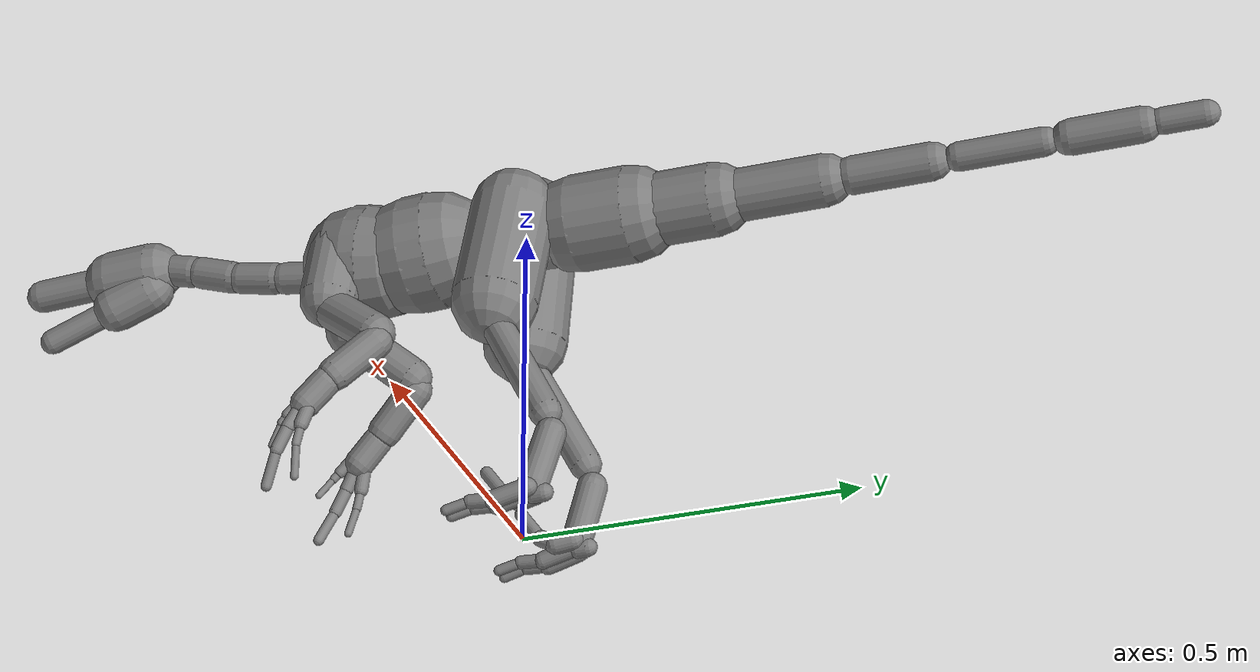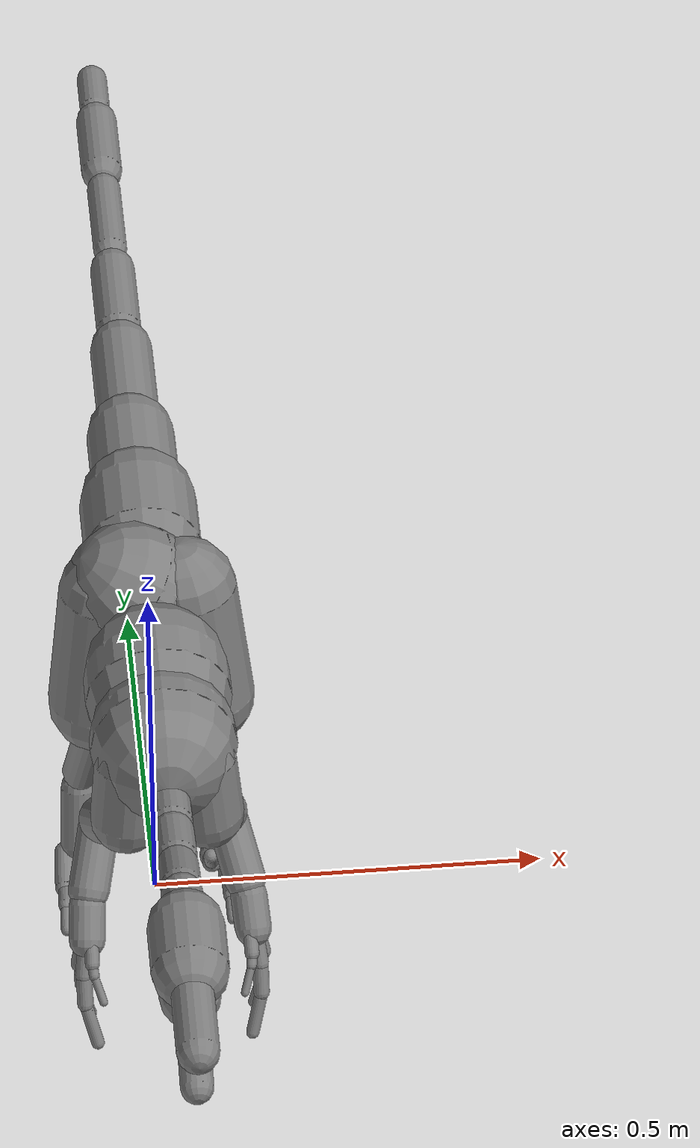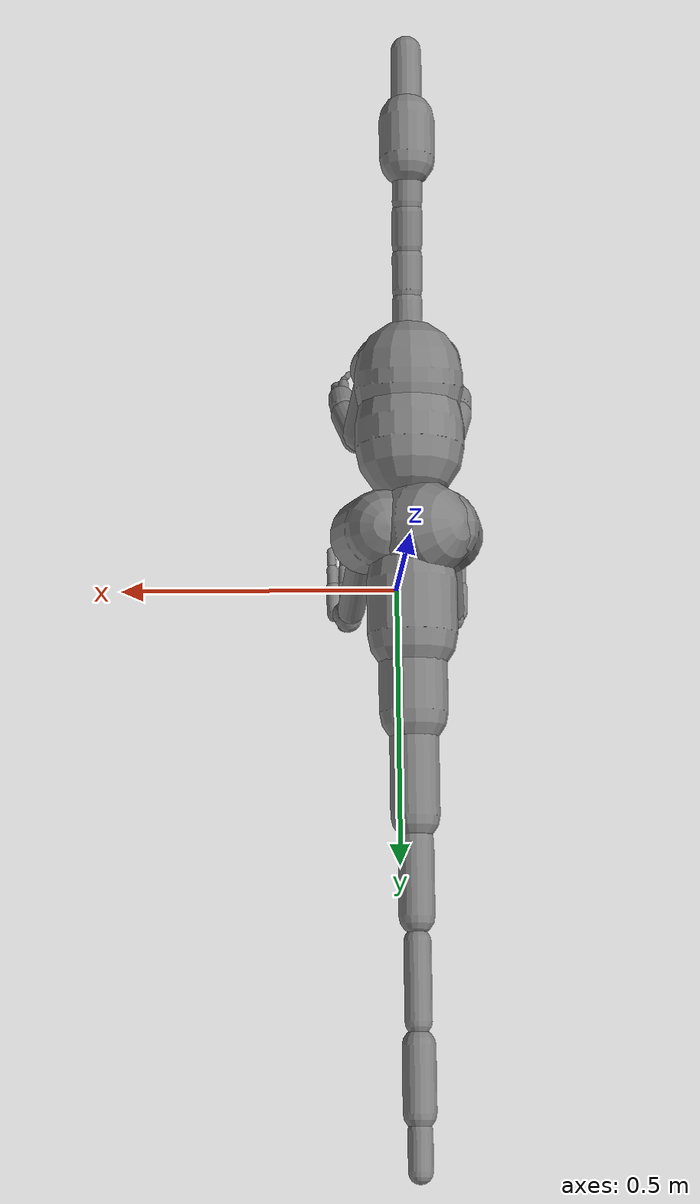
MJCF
<mujoco model="raptor">
  <compiler angle="radian" />
  <option timestep="0.016667" />
  <contact>
    <exclude body1="Neck3" body2="Jaw" />
    <exclude body1="LeftUpLeg" body2="Hips" />
    <exclude body1="LeftUpLeg" body2="Spine" />
    <exclude body1="LeftUpLeg" body2="Spine1" />
    <exclude body1="LeftUpLeg" body2="Tail" />
    <exclude body1="RightUpLeg" body2="Hips" />
    <exclude body1="RightUpLeg" body2="Spine" />
    <exclude body1="RightUpLeg" body2="Spine1" />
    <exclude body1="RightUpLeg" body2="Tail" />
    <exclude body1="LeftUpLeg" body2="RightUpLeg" />
    <exclude body1="LeftShoulder" body2="Spine" />
    <exclude body1="LeftShoulder" body2="Spine1" />
    <exclude body1="LeftShoulder" body2="Neck" />
    <exclude body1="LeftShoulder" body2="Hips" />
    <exclude body1="LeftToeBase" body2="LeftFootIndex1" />
    <exclude body1="LeftToeBase" body2="LeftFootMiddle1" />
    <exclude body1="LeftToeBase" body2="LeftFootRing1" />
    <exclude body1="LeftFootIndex1" body2="LeftFootMiddle1" />
    <exclude body1="LeftFootMiddle1" body2="LeftFootRing1" />
    <exclude body1="LeftFootIndex1" body2="LeftFootRing1" />
    <exclude body1="LeftFootIndex2" body2="LeftFootMiddle1" />
    <exclude body1="LeftFoot" body2="LeftFootIndex2" />
    <exclude body1="LeftHandMiddle2" body2="LeftHandRing2" />
    <exclude body1="LeftHandMiddle2" body2="LeftHandRing3" />
    <exclude body1="LeftHandMiddle3" body2="LeftHandRing3" />
    <exclude body1="RightShoulder" body2="Spine" />
    <exclude body1="RightShoulder" body2="Spine1" />
    <exclude body1="RightShoulder" body2="Neck" />
    <exclude body1="RightShoulder" body2="Hips" />
    <exclude body1="RightToeBase" body2="RightFootIndex1" />
    <exclude body1="RightToeBase" body2="RightFootMiddle1" />
    <exclude body1="RightToeBase" body2="RightFootRing1" />
    <exclude body1="RightFootIndex1" body2="RightFootMiddle1" />
    <exclude body1="RightFootMiddle1" body2="RightFootRing1" />
    <exclude body1="RightFootIndex1" body2="RightFootRing1" />
    <exclude body1="RightFootIndex2" body2="RightFootMiddle1" />
    <exclude body1="RightFoot" body2="RightFootIndex2" />
    <exclude body1="RightHandMiddle2" body2="RightHandRing2" />
    <exclude body1="RightHandMiddle2" body2="RightHandRing3" />
    <exclude body1="RightHandMiddle3" body2="RightHandRing3" />
    <exclude body1="LeftShoulder" body2="RightShoulder" />
  </contact>
  <worldbody>
    <body name="Hips" pos="0 0.001235 0.51128">
      <geom name="g_Hips" fromto="-0.0051561 -0.00011752 0.0044872 -0.021484 -0.00048968 0.018697" size="0.08000" density="1401.8" type="capsule" contype="1" conaffinity="1" friction="1.0 0.05 0.05" />
      <body name="Spine" pos="-3.9443e-33 -0.12801 -0.0030721">
        <joint name="Spine_x" type="hinge" axis="1 0 0" pos="0 0 0" range="-1.5107 0.6132" limited="true" armature="0.02" frictionloss="0.1" />
        <joint name="Spine_y" type="hinge" axis="0 1 0" pos="0 0 0" range="-0.6056 0.6056" limited="true" armature="0.02" frictionloss="0.1" />
        <joint name="Spine_z" type="hinge" axis="0 0 1" pos="0 0 0" range="-0.6850 0.6850" limited="true" armature="0.02" frictionloss="0.1" />
        <geom name="g_Spine" fromto="-4.8665e-10 -0.013026 -0.00061441 -2.0277e-09 -0.054274 -0.0025601" size="0.09" density="980.8" type="capsule" contype="1" conaffinity="1" friction="1.0 0.05 0.05" />
        <body name="Spine1" pos="-4.0554e-09 -0.10855 -0.0051201">
          <joint name="Spine1_x" type="hinge" axis="1 0 0" pos="0 0 0" range="-1.0496 0.7756" limited="true" armature="0.02" frictionloss="0.1" />
          <joint name="Spine1_y" type="hinge" axis="0 1 0" pos="0 0 0" range="-0.8858 0.8858" limited="true" armature="0.02" frictionloss="0.1" />
          <joint name="Spine1_z" type="hinge" axis="0 0 1" pos="0 0 0" range="-0.7553 0.7553" limited="true" armature="0.02" frictionloss="0.1" />
          <geom name="g_Spine1" fromto="-2.2009e-09 -0.0078902 0.0010698 -9.1703e-09 -0.032876 0.0044577" size="0.09" density="984.0" type="capsule" contype="1" conaffinity="1" friction="1.0 0.05 0.05" />
          <body name="Neck" pos="-3.4457e-09 -0.092164 -0.0071682">
            <joint name="Neck_x" type="hinge" axis="1 0 0" pos="0 0 0" range="-1.4389 0.8324" limited="true" armature="0.02" frictionloss="0.1" />
            <joint name="Neck_y" type="hinge" axis="0 1 0" pos="0 0 0" range="-0.6063 0.8743" limited="true" armature="0.02" frictionloss="0.1" />
            <joint name="Neck_z" type="hinge" axis="0 0 1" pos="0 0 0" range="-0.8974 0.8974" limited="true" armature="0.02" frictionloss="0.1" />
            <geom name="g_Neck" fromto="-3.3633e-10 -0.0090436 0.0013273 -2.4664e-09 -0.06632 0.0097334" size="0.025" density="980.8" type="capsule" contype="1" conaffinity="1" friction="1.0 0.05 0.05" />
            <body name="Neck1" pos="-2.8027e-09 -0.075363 0.011061">
              <joint name="Neck1_x" type="hinge" axis="1 0 0" pos="0 0 0" range="-1.2515 0.7095" limited="true" armature="0.02" frictionloss="0.1" />
              <joint name="Neck1_y" type="hinge" axis="0 1 0" pos="0 0 0" range="-0.7888 0.7888" limited="true" armature="0.02" frictionloss="0.1" />
              <joint name="Neck1_z" type="hinge" axis="0 0 1" pos="0 0 0" range="-0.6976 0.7484" limited="true" armature="0.02" frictionloss="0.1" />
              <geom name="g_Neck1" fromto="-3.2568e-10 -0.0087686 0.0017671 -2.3883e-09 -0.064303 0.012959" size="0.025" density="984.0" type="capsule" contype="1" conaffinity="1" friction="1.0 0.05 0.05" />
              <body name="Neck2" pos="-2.714e-09 -0.073072 0.014726">
                <joint name="Neck2_x" type="hinge" axis="1 0 0" pos="0 0 0" range="-0.9083 1.7995" limited="true" armature="0.02" frictionloss="0.1" />
                <joint name="Neck2_y" type="hinge" axis="0 1 0" pos="0 0 0" range="-0.6279 0.5475" limited="true" armature="0.02" frictionloss="0.1" />
                <joint name="Neck2_z" type="hinge" axis="0 0 1" pos="0 0 0" range="-0.9775 0.9775" limited="true" armature="0.02" frictionloss="0.1" />
                <geom name="g_Neck2" fromto="-3.1245e-10 -0.0084403 0.0028832 -2.2913e-09 -0.061896 0.021143" size="0.025" density="984.0" type="capsule" contype="1" conaffinity="1" friction="1.0 0.05 0.05" />
                <body name="Neck3" pos="-2.6037e-09 -0.070336 0.024026">
                  <joint name="Neck3_x" type="hinge" axis="1 0 0" pos="0 0 0" range="-0.7080 1.5979" limited="true" armature="0.02" frictionloss="0.1" />
                  <joint name="Neck3_y" type="hinge" axis="0 1 0" pos="0 0 0" range="-0.7589 1.6128" limited="true" armature="0.02" frictionloss="0.1" />
                  <joint name="Neck3_z" type="hinge" axis="0 0 1" pos="0 0 0" range="-0.8767 0.8654" limited="true" armature="0.02" frictionloss="0.1" />
                  <geom name="g_Neck3" fromto="-2.9566e-05 -0.0069161 0.0018385 -0.00021682 -0.050718 0.013483" size="0.025" density="984.0" type="capsule" contype="1" conaffinity="1" friction="1.0 0.05 0.05" />
                  <body name="Head" pos="-0.00024638 -0.057634 0.015321">
                    <joint name="Head_x" type="hinge" axis="1 0 0" pos="0 0 0" range="-1.6792 1.7949" limited="true" armature="0.02" frictionloss="0.1" />
                    <joint name="Head_y" type="hinge" axis="0 1 0" pos="0 0 0" range="-1.4589 1.4589" limited="true" armature="0.02" frictionloss="0.1" />
                    <joint name="Head_z" type="hinge" axis="0 0 1" pos="0 0 0" range="-1.6584 1.6584" limited="true" armature="0.02" frictionloss="0.1" />
                    <geom name="g_Head" fromto="-0.0001156 -0.0184456 -0.000684256 -0.0005491 -0.0876166 -0.00325022" size="0.04620" density="980.8" type="capsule" contype="1" conaffinity="1" friction="1.0 0.05 0.05" />
                    <geom name="g_Head_muzzle" fromto="-0.0007225 -0.115285 -0.0042766 -0.0013294 -0.212124 -0.00786894" size="0.02550" density="980.8" type="capsule" contype="1" conaffinity="1" friction="1.0 0.05 0.05" />
                    <body name="Jaw" pos="-0.00022066 -0.006775 -0.027347">
                      <joint name="Jaw_x" type="hinge" axis="1 0 0" pos="0 0 0" range="-0.5242 1.3148" limited="true" armature="0.02" frictionloss="0.1" />
                      <joint name="Jaw_y" type="hinge" axis="0 1 0" pos="0 0 0" range="-0.6722 0.6722" limited="true" armature="0.02" frictionloss="0.1" />
                      <joint name="Jaw_z" type="hinge" axis="0 0 1" pos="0 0 0" range="-0.6218 0.6218" limited="true" armature="0.02" frictionloss="0.1" />
                      <geom name="g_Jaw" fromto="-0.000129808 -0.0153616 -0.00566928 -0.000616588 -0.0729676 -0.0269291" size="0.03670" density="980.8" type="capsule" contype="1" conaffinity="1" friction="1.0 0.05 0.05" />
                      <geom name="g_Jaw_tip" fromto="-0.0008113 -0.09601 -0.035433 -0.00152524 -0.180499 -0.066614" size="0.01980" density="980.8" type="capsule" contype="1" conaffinity="1" friction="1.0 0.05 0.05" />
                    </body>
                  </body>
                </body>
              </body>
            </body>
          </body>
          <body name="LeftShoulder" pos="0.04014 -0.052546 0.016957">
            <joint name="LeftShoulder_x" type="hinge" axis="1 0 0" pos="0 0 0" range="-1.0879 1.3179" limited="true" armature="0.02" frictionloss="0.1" />
            <joint name="LeftShoulder_y" type="hinge" axis="0 1 0" pos="0 0 0" range="-0.9148 0.7142" limited="true" armature="0.02" frictionloss="0.1" />
            <joint name="LeftShoulder_z" type="hinge" axis="0 0 1" pos="0 0 0" range="-0.6609 0.5530" limited="true" armature="0.02" frictionloss="0.1" />
            <geom name="g_LeftShoulder" fromto="0.001229 -0.0013909 -0.013008 0.009013 -0.0102 -0.095396" size="0.04500" density="1401.8" type="capsule" contype="1" conaffinity="1" friction="1.0 0.05 0.05" />
            <body name="LeftArm" pos="0.010242 -0.01159 -0.1084">
              <joint name="LeftArm_x" type="hinge" axis="1 0 0" pos="0 0 0" range="-2.1802 2.3641" limited="true" armature="0.02" frictionloss="0.1" />
              <joint name="LeftArm_y" type="hinge" axis="0 1 0" pos="0 0 0" range="-1.3899 1.6724" limited="true" armature="0.02" frictionloss="0.1" />
              <joint name="LeftArm_z" type="hinge" axis="0 0 1" pos="0 0 0" range="-2.2335 1.9332" limited="true" armature="0.02" frictionloss="0.1" />
              <geom name="g_LeftArm" fromto="0.0032047 0.012225 -0.010312 0.023501 0.08965 -0.075621" size="0.03100" density="1401.8" type="capsule" contype="1" conaffinity="1" friction="1.0 0.05 0.05" />
              <body name="LeftForeArm" pos="0.026706 0.10187 -0.085933">
                <joint name="LeftForeArm_x" type="hinge" axis="1 0 0" pos="0 0 0" range="-1.2770 1.8986" limited="true" armature="0.02" frictionloss="0.1" />
                <joint name="LeftForeArm_y" type="hinge" axis="0 1 0" pos="0 0 0" range="-1.2931 1.1387" limited="true" armature="0.02" frictionloss="0.1" />
                <joint name="LeftForeArm_z" type="hinge" axis="0 0 1" pos="0 0 0" range="-2.5874 1.4681" limited="true" armature="0.02" frictionloss="0.1" />
                <geom name="g_LeftForeArm" fromto="0.0026862 -0.0086777 -0.0082469 0.019699 -0.063637 -0.060478" size="0.02600" density="1401.8" type="capsule" contype="1" conaffinity="1" friction="1.0 0.05 0.05" />
                <body name="LeftHand" pos="0.022385 -0.072314 -0.068724">
                  <joint name="LeftHand_x" type="hinge" axis="1 0 0" pos="0 0 0" range="-3.1067 2.0532" limited="true" armature="0.02" frictionloss="0.1" />
                  <joint name="LeftHand_y" type="hinge" axis="0 1 0" pos="0 0 0" range="-1.6520 1.3623" limited="true" armature="0.02" frictionloss="0.1" />
                  <joint name="LeftHand_z" type="hinge" axis="0 0 1" pos="0 0 0" range="-3.1067 2.6298" limited="true" armature="0.02" frictionloss="0.1" />
                  <geom name="g_LeftHand" fromto="0.00046469 -0.0045512 -0.0049138 0.0034077 -0.033375 -0.036034" size="0.02300" density="1401.8" type="capsule" contype="1" conaffinity="1" friction="1.0 0.05 0.05" />
                  <body name="LeftHandMiddle1" pos="0.005367 -0.039467 -0.042337">
                    <joint name="LeftHandMiddle1_x" type="hinge" axis="1 0 0" pos="0 0 0" range="-1.0460 1.4460" limited="true" armature="0.02" frictionloss="0.1" />
                    <joint name="LeftHandMiddle1_y" type="hinge" axis="0 1 0" pos="0 0 0" range="-1.2524 1.1571" limited="true" armature="0.02" frictionloss="0.1" />
                    <joint name="LeftHandMiddle1_z" type="hinge" axis="0 0 1" pos="0 0 0" range="-2.0143 1.1108" limited="true" armature="0.02" frictionloss="0.1" />
                    <geom name="g_LeftHandMiddle1" fromto="0 0 0 0.0046945 -0.01706 -0.03221" size="0.01071" density="1310.9" type="capsule" contype="1" conaffinity="1" friction="1.0 0.05 0.05" />
                    <body name="LeftHandMiddle2" pos="0.0046945 -0.01706 -0.03221">
                      <joint name="LeftHandMiddle2_x" type="hinge" axis="1 0 0" pos="0 0 0" range="-0.2083 0.6642" limited="true" armature="0.02" frictionloss="0.1" />
                      <joint name="LeftHandMiddle2_y" type="hinge" axis="0 1 0" pos="0 0 0" range="-0.2988 0.9734" limited="true" armature="0.02" frictionloss="0.1" />
                      <joint name="LeftHandMiddle2_z" type="hinge" axis="0 0 1" pos="0 0 0" range="-0.8469 0.2330" limited="true" armature="0.02" frictionloss="0.1" />
                      <geom name="g_LeftHandMiddle2" fromto="0 0 0 -0.00016794 -0.016683 -0.034806" size="0.00996" density="1310.9" type="capsule" contype="1" conaffinity="1" friction="1.0 0.05 0.05" />
                      <body name="LeftHandMiddle3" pos="-0.00016794 -0.016683 -0.034806">
                        <joint name="LeftHandMiddle3_x" type="hinge" axis="1 0 0" pos="0 0 0" range="-0.2106 1.5778" limited="true" armature="0.02" frictionloss="0.1" />
                        <joint name="LeftHandMiddle3_y" type="hinge" axis="0 1 0" pos="0 0 0" range="-0.4369 1.1254" limited="true" armature="0.02" frictionloss="0.1" />
                        <joint name="LeftHandMiddle3_z" type="hinge" axis="0 0 1" pos="0 0 0" range="-1.8404 0.2958" limited="true" armature="0.02" frictionloss="0.1" />
                        <geom name="g_LeftHandMiddle3" fromto="-0.00193916 -0.00294847 -0.00741284 -0.0130129 -0.0197859 -0.0497443" size="0.00821" density="1310.9" type="capsule" contype="1" conaffinity="1" friction="1.0 0.05 0.05" />
                      </body>
                    </body>
                  </body>
                  <body name="LeftHandRing1" pos="0.0074586 -0.0274 -0.046892">
                    <joint name="LeftHandRing1_x" type="hinge" axis="1 0 0" pos="0 0 0" range="-1.0420 0.9748" limited="true" armature="0.02" frictionloss="0.1" />
                    <joint name="LeftHandRing1_y" type="hinge" axis="0 1 0" pos="0 0 0" range="-0.8982 1.2482" limited="true" armature="0.02" frictionloss="0.1" />
                    <joint name="LeftHandRing1_z" type="hinge" axis="0 0 1" pos="0 0 0" range="-1.4353 1.0217" limited="true" armature="0.02" frictionloss="0.1" />
                    <geom name="g_LeftHandRing1" fromto="0 0 0 0.0066506 -0.0069127 -0.029525" size="0.01092" density="1310.9" type="capsule" contype="1" conaffinity="1" friction="1.0 0.05 0.05" />
                    <body name="LeftHandRing2" pos="0.0066506 -0.0069127 -0.029525">
                      <joint name="LeftHandRing2_x" type="hinge" axis="1 0 0" pos="0 0 0" range="-0.2026 0.6074" limited="true" armature="0.02" frictionloss="0.1" />
                      <joint name="LeftHandRing2_y" type="hinge" axis="0 1 0" pos="0 0 0" range="-0.3775 1.2035" limited="true" armature="0.02" frictionloss="0.1" />
                      <joint name="LeftHandRing2_z" type="hinge" axis="0 0 1" pos="0 0 0" range="-0.6580 0.2258" limited="true" armature="0.02" frictionloss="0.1" />
                      <geom name="g_LeftHandRing2" fromto="0 0 0 0.00042298 -0.0061192 -0.030642" size="0.00672" density="1310.9" type="capsule" contype="1" conaffinity="1" friction="1.0 0.05 0.05" />
                      <body name="LeftHandRing3" pos="0.00042298 -0.0061192 -0.030642">
                        <joint name="LeftHandRing3_x" type="hinge" axis="1 0 0" pos="0 0 0" range="-0.1917 2.2210" limited="true" armature="0.02" frictionloss="0.1" />
                        <joint name="LeftHandRing3_y" type="hinge" axis="0 1 0" pos="0 0 0" range="-0.3447 1.4237" limited="true" armature="0.02" frictionloss="0.1" />
                        <joint name="LeftHandRing3_z" type="hinge" axis="0 0 1" pos="0 0 0" range="-2.2882 0.2091" limited="true" armature="0.02" frictionloss="0.1" />
                        <geom name="g_LeftHandRing3" fromto="-0.00166988 -0.000810042 -0.00570573 -0.0134546 -0.00652669 -0.0459723" size="0.00600" density="1310.9" type="capsule" contype="1" conaffinity="1" friction="1.0 0.05 0.05" />
                      </body>
                    </body>
                  </body>
                  <body name="LeftHandIndex1" pos="-0.0012083 -0.046912 -0.033616">
                    <joint name="LeftHandIndex1_x" type="hinge" axis="1 0 0" pos="0 0 0" range="-1.0547 0.9737" limited="true" armature="0.02" frictionloss="0.1" />
                    <joint name="LeftHandIndex1_y" type="hinge" axis="0 1 0" pos="0 0 0" range="-0.5403 1.1295" limited="true" armature="0.02" frictionloss="0.1" />
                    <joint name="LeftHandIndex1_z" type="hinge" axis="0 0 1" pos="0 0 0" range="-1.0749 0.9371" limited="true" armature="0.02" frictionloss="0.1" />
                    <geom name="g_LeftHandIndex1" fromto="0 0 0 0.00054082 -0.016357 -0.01549" size="0.00906" density="1310.9" type="capsule" contype="1" conaffinity="1" friction="1.0 0.05 0.05" />
                    <body name="LeftHandIndex2" pos="0.00054082 -0.016357 -0.01549">
                      <joint name="LeftHandIndex2_x" type="hinge" axis="1 0 0" pos="0 0 0" range="-0.2408 0.5086" limited="true" armature="0.02" frictionloss="0.1" />
                      <joint name="LeftHandIndex2_y" type="hinge" axis="0 1 0" pos="0 0 0" range="-0.2930 0.4743" limited="true" armature="0.02" frictionloss="0.1" />
                      <joint name="LeftHandIndex2_z" type="hinge" axis="0 0 1" pos="0 0 0" range="-0.6024 0.2600" limited="true" armature="0.02" frictionloss="0.1" />
                      <geom name="g_LeftHandIndex2" fromto="0 0 0 -0.0013763 -0.0097047 -0.010564" size="0.00653" density="1310.9" type="capsule" contype="1" conaffinity="1" friction="1.0 0.05 0.05" />
                      <body name="LeftHandIndex3" pos="-0.0013763 -0.0097047 -0.010564">
                        <joint name="LeftHandIndex3_x" type="hinge" axis="1 0 0" pos="0 0 0" range="-0.2702 1.6488" limited="true" armature="0.02" frictionloss="0.1" />
                        <joint name="LeftHandIndex3_y" type="hinge" axis="0 1 0" pos="0 0 0" range="-0.3272 0.5907" limited="true" armature="0.02" frictionloss="0.1" />
                        <joint name="LeftHandIndex3_z" type="hinge" axis="0 0 1" pos="0 0 0" range="-1.9297 0.3181" limited="true" armature="0.02" frictionloss="0.1" />
                        <geom name="g_LeftHandIndex3" fromto="-0.00143563 -0.00273366 -0.00420885 -0.00987819 -0.0188095 -0.0289599" size="0.00522" density="1310.9" type="capsule" contype="1" conaffinity="1" friction="1.0 0.05 0.05" />
                      </body>
                    </body>
                  </body>
                </body>
              </body>
            </body>
          </body>
          <body name="RightShoulder" pos="-0.04014 -0.052546 0.016957">
            <joint name="RightShoulder_x" type="hinge" axis="1 0 0" pos="0 0 0" range="-1.0879 1.3179" limited="true" armature="0.02" frictionloss="0.1" />
            <joint name="RightShoulder_y" type="hinge" axis="0 1 0" pos="0 0 0" range="-0.7142 1.0588" limited="true" armature="0.02" frictionloss="0.1" />
            <joint name="RightShoulder_z" type="hinge" axis="0 0 1" pos="0 0 0" range="-0.5530 0.6609" limited="true" armature="0.02" frictionloss="0.1" />
            <geom name="g_RightShoulder" fromto="-0.001229 -0.0013908 -0.013008 -0.009013 -0.010199 -0.095396" size="0.04500" density="1401.8" type="capsule" contype="1" conaffinity="1" friction="1.0 0.05 0.05" />
            <body name="RightArm" pos="-0.010242 -0.01159 -0.1084">
              <joint name="RightArm_x" type="hinge" axis="1 0 0" pos="0 0 0" range="-2.1802 2.3641" limited="true" armature="0.02" frictionloss="0.1" />
              <joint name="RightArm_y" type="hinge" axis="0 1 0" pos="0 0 0" range="-1.6724 1.3899" limited="true" armature="0.02" frictionloss="0.1" />
              <joint name="RightArm_z" type="hinge" axis="0 0 1" pos="0 0 0" range="-1.9332 2.2335" limited="true" armature="0.02" frictionloss="0.1" />
              <geom name="g_RightArm" fromto="-0.0032047 0.012225 -0.010312 -0.023501 0.089649 -0.075621" size="0.03100" density="1401.8" type="capsule" contype="1" conaffinity="1" friction="1.0 0.05 0.05" />
              <body name="RightForeArm" pos="-0.026705 0.10187 -0.085933">
                <joint name="RightForeArm_x" type="hinge" axis="1 0 0" pos="0 0 0" range="-1.2770 1.8986" limited="true" armature="0.02" frictionloss="0.1" />
                <joint name="RightForeArm_y" type="hinge" axis="0 1 0" pos="0 0 0" range="-1.1387 1.2931" limited="true" armature="0.02" frictionloss="0.1" />
                <joint name="RightForeArm_z" type="hinge" axis="0 0 1" pos="0 0 0" range="-1.4115 2.5874" limited="true" armature="0.02" frictionloss="0.1" />
                <geom name="g_RightForeArm" fromto="-0.0026862 -0.0086777 -0.0082469 -0.019699 -0.063636 -0.060477" size="0.02600" density="1401.8" type="capsule" contype="1" conaffinity="1" friction="1.0 0.05 0.05" />
                <body name="RightHand" pos="-0.022385 -0.072314 -0.068724">
                  <joint name="RightHand_x" type="hinge" axis="1 0 0" pos="0 0 0" range="-3.1067 2.0532" limited="true" armature="0.02" frictionloss="0.1" />
                  <joint name="RightHand_y" type="hinge" axis="0 1 0" pos="0 0 0" range="-1.3623 1.6520" limited="true" armature="0.02" frictionloss="0.1" />
                  <joint name="RightHand_z" type="hinge" axis="0 0 1" pos="0 0 0" range="-2.6298 3.1067" limited="true" armature="0.02" frictionloss="0.1" />
                  <geom name="g_RightHand" fromto="-0.00046471 -0.0045512 -0.0049138 -0.0034078 -0.033375 -0.036035" size="0.02300" density="1401.8" type="capsule" contype="1" conaffinity="1" friction="1.0 0.05 0.05" />
                  <body name="RightHandMiddle1" pos="-0.005367 -0.039467 -0.042337">
                    <joint name="RightHandMiddle1_x" type="hinge" axis="1 0 0" pos="0 0 0" range="-1.0460 1.4460" limited="true" armature="0.02" frictionloss="0.1" />
                    <joint name="RightHandMiddle1_y" type="hinge" axis="0 1 0" pos="0 0 0" range="-1.1571 1.2524" limited="true" armature="0.02" frictionloss="0.1" />
                    <joint name="RightHandMiddle1_z" type="hinge" axis="0 0 1" pos="0 0 0" range="-1.1108 2.0143" limited="true" armature="0.02" frictionloss="0.1" />
                    <geom name="g_RightHandMiddle1" fromto="0 0 0 -0.0046947 -0.01706 -0.032209" size="0.01071" density="1310.9" type="capsule" contype="1" conaffinity="1" friction="1.0 0.05 0.05" />
                    <body name="RightHandMiddle2" pos="-0.0046947 -0.01706 -0.032209">
                      <joint name="RightHandMiddle2_x" type="hinge" axis="1 0 0" pos="0 0 0" range="-0.2083 0.6642" limited="true" armature="0.02" frictionloss="0.1" />
                      <joint name="RightHandMiddle2_y" type="hinge" axis="0 1 0" pos="0 0 0" range="-0.9734 0.2988" limited="true" armature="0.02" frictionloss="0.1" />
                      <joint name="RightHandMiddle2_z" type="hinge" axis="0 0 1" pos="0 0 0" range="-0.2330 0.8469" limited="true" armature="0.02" frictionloss="0.1" />
                      <geom name="g_RightHandMiddle2" fromto="0 0 0 0.00016794 -0.016683 -0.034806" size="0.00996" density="1310.9" type="capsule" contype="1" conaffinity="1" friction="1.0 0.05 0.05" />
                      <body name="RightHandMiddle3" pos="0.00016794 -0.016683 -0.034806">
                        <joint name="RightHandMiddle3_x" type="hinge" axis="1 0 0" pos="0 0 0" range="-0.2106 1.5778" limited="true" armature="0.02" frictionloss="0.1" />
                        <joint name="RightHandMiddle3_y" type="hinge" axis="0 1 0" pos="0 0 0" range="-1.1254 0.4369" limited="true" armature="0.02" frictionloss="0.1" />
                        <joint name="RightHandMiddle3_z" type="hinge" axis="0 0 1" pos="0 0 0" range="-0.2958 1.8404" limited="true" armature="0.02" frictionloss="0.1" />
                        <geom name="g_RightHandMiddle3" fromto="0.00193918 -0.00294852 -0.00741282 0.0130131 -0.0197864 -0.0497447" size="0.00821" density="1310.9" type="capsule" contype="1" conaffinity="1" friction="1.0 0.05 0.05" />
                      </body>
                    </body>
                  </body>
                  <body name="RightHandRing1" pos="-0.0074589 -0.0274 -0.046892">
                    <joint name="RightHandRing1_x" type="hinge" axis="1 0 0" pos="0 0 0" range="-1.0420 0.9748" limited="true" armature="0.02" frictionloss="0.1" />
                    <joint name="RightHandRing1_y" type="hinge" axis="0 1 0" pos="0 0 0" range="-1.2482 0.8982" limited="true" armature="0.02" frictionloss="0.1" />
                    <joint name="RightHandRing1_z" type="hinge" axis="0 0 1" pos="0 0 0" range="-1.0217 1.4353" limited="true" armature="0.02" frictionloss="0.1" />
                    <geom name="g_RightHandRing1" fromto="0 0 0 -0.0066498 -0.006913 -0.029525" size="0.01076" density="1310.9" type="capsule" contype="1" conaffinity="1" friction="1.0 0.05 0.05" />
                    <body name="RightHandRing2" pos="-0.0066498 -0.006913 -0.029525">
                      <joint name="RightHandRing2_x" type="hinge" axis="1 0 0" pos="0 0 0" range="-0.2026 0.6074" limited="true" armature="0.02" frictionloss="0.1" />
                      <joint name="RightHandRing2_y" type="hinge" axis="0 1 0" pos="0 0 0" range="-1.2035 0.3760" limited="true" armature="0.02" frictionloss="0.1" />
                      <joint name="RightHandRing2_z" type="hinge" axis="0 0 1" pos="0 0 0" range="-0.2258 0.6580" limited="true" armature="0.02" frictionloss="0.1" />
                      <geom name="g_RightHandRing2" fromto="0 0 0 -0.0004231 -0.0061191 -0.030642" size="0.00672" density="1310.9" type="capsule" contype="1" conaffinity="1" friction="1.0 0.05 0.05" />
                      <body name="RightHandRing3" pos="-0.0004231 -0.0061191 -0.030642">
                        <joint name="RightHandRing3_x" type="hinge" axis="1 0 0" pos="0 0 0" range="-0.1917 2.2210" limited="true" armature="0.02" frictionloss="0.1" />
                        <joint name="RightHandRing3_y" type="hinge" axis="0 1 0" pos="0 0 0" range="-1.4237 0.3447" limited="true" armature="0.02" frictionloss="0.1" />
                        <joint name="RightHandRing3_z" type="hinge" axis="0 0 1" pos="0 0 0" range="-0.2091 2.2882" limited="true" armature="0.02" frictionloss="0.1" />
                        <geom name="g_RightHandRing3" fromto="0.00166986 -0.000810038 -0.00570573 0.0134544 -0.00652662 -0.0459721" size="0.00600" density="1310.9" type="capsule" contype="1" conaffinity="1" friction="1.0 0.05 0.05" />
                      </body>
                    </body>
                  </body>
                  <body name="RightHandIndex1" pos="0.0012082 -0.046912 -0.033616">
                    <joint name="RightHandIndex1_x" type="hinge" axis="1 0 0" pos="0 0 0" range="-1.0547 0.9737" limited="true" armature="0.02" frictionloss="0.1" />
                    <joint name="RightHandIndex1_y" type="hinge" axis="0 1 0" pos="0 0 0" range="-1.1295 0.5403" limited="true" armature="0.02" frictionloss="0.1" />
                    <joint name="RightHandIndex1_z" type="hinge" axis="0 0 1" pos="0 0 0" range="-0.9371 1.0749" limited="true" armature="0.02" frictionloss="0.1" />
                    <geom name="g_RightHandIndex1" fromto="0 0 0 -0.00054081 -0.016357 -0.01549" size="0.00906" density="1310.9" type="capsule" contype="1" conaffinity="1" friction="1.0 0.05 0.05" />
                    <body name="RightHandIndex2" pos="-0.00054081 -0.016357 -0.01549">
                      <joint name="RightHandIndex2_x" type="hinge" axis="1 0 0" pos="0 0 0" range="-0.2408 0.5086" limited="true" armature="0.02" frictionloss="0.1" />
                      <joint name="RightHandIndex2_y" type="hinge" axis="0 1 0" pos="0 0 0" range="-0.4743 0.2930" limited="true" armature="0.02" frictionloss="0.1" />
                      <joint name="RightHandIndex2_z" type="hinge" axis="0 0 1" pos="0 0 0" range="-0.2600 0.6024" limited="true" armature="0.02" frictionloss="0.1" />
                      <geom name="g_RightHandIndex2" fromto="0 0 0 0.0013764 -0.0097051 -0.010563" size="0.00653" density="1310.9" type="capsule" contype="1" conaffinity="1" friction="1.0 0.05 0.05" />
                      <body name="RightHandIndex3" pos="0.0013764 -0.0097051 -0.010563">
                        <joint name="RightHandIndex3_x" type="hinge" axis="1 0 0" pos="0 0 0" range="-0.2702 1.6488" limited="true" armature="0.02" frictionloss="0.1" />
                        <joint name="RightHandIndex3_y" type="hinge" axis="0 1 0" pos="0 0 0" range="-0.5907 0.3272" limited="true" armature="0.02" frictionloss="0.1" />
                        <joint name="RightHandIndex3_z" type="hinge" axis="0 0 1" pos="0 0 0" range="-0.3181 1.9297" limited="true" armature="0.02" frictionloss="0.1" />
                        <geom name="g_RightHandIndex3" fromto="0.00143563 -0.00273363 -0.00420888 0.00987822 -0.0188095 -0.0289603" size="0.00522" density="1310.9" type="capsule" contype="1" conaffinity="1" friction="1.0 0.05 0.05" />
                      </body>
                    </body>
                  </body>
                </body>
              </body>
            </body>
          </body>
        </body>
      </body>
      <body name="Tail" pos="0 0.066018 -0.0008208">
        <joint name="Tail_x" type="hinge" axis="1 0 0" pos="0 0 0" range="-0.6016 1.2474" limited="true" armature="0.02" frictionloss="0.1" />
        <joint name="Tail_y" type="hinge" axis="0 1 0" pos="0 0 0" range="-1.1216 1.1216" limited="true" armature="0.02" frictionloss="0.1" />
        <joint name="Tail_z" type="hinge" axis="0 0 1" pos="0 0 0" range="-0.9570 0.9570" limited="true" armature="0.02" frictionloss="0.1" />
        <geom name="g_Tail" fromto="-4.5355e-10 0.014039 -5.9088e-05 -3.326e-09 0.10295 -0.00043331" size="0.07400" density="1401.8" type="capsule" contype="1" conaffinity="1" friction="1.0 0.05 0.05" />
        <body name="Tail1" pos="-3.7796e-09 0.11699 -0.0004924">
          <joint name="Tail1_x" type="hinge" axis="1 0 0" pos="0 0 0" range="-0.4449 0.8159" limited="true" armature="0.02" frictionloss="0.1" />
          <joint name="Tail1_y" type="hinge" axis="0 1 0" pos="0 0 0" range="-0.8186 0.8186" limited="true" armature="0.02" frictionloss="0.1" />
          <joint name="Tail1_z" type="hinge" axis="0 0 1" pos="0 0 0" range="-0.6087 0.6087" limited="true" armature="0.02" frictionloss="0.1" />
          <geom name="g_Tail1" fromto="-5.0601e-10 0.015662 -6.5987e-05 -3.7107e-09 0.11486 -0.00048391" size="0.05600" density="1401.8" type="capsule" contype="1" conaffinity="1" friction="1.0 0.05 0.05" />
          <body name="Tail2" pos="-4.2167e-09 0.13052 -0.0005499">
            <joint name="Tail2_x" type="hinge" axis="1 0 0" pos="0 0 0" range="-0.4246 0.4704" limited="true" armature="0.02" frictionloss="0.1" />
            <joint name="Tail2_y" type="hinge" axis="0 1 0" pos="0 0 0" range="-0.4631 0.4631" limited="true" armature="0.02" frictionloss="0.1" />
            <joint name="Tail2_z" type="hinge" axis="0 0 1" pos="0 0 0" range="-0.4904 0.4904" limited="true" armature="0.02" frictionloss="0.1" />
            <geom name="g_Tail2" fromto="-6.7061e-10 0.020757 -8.7363e-05 -4.9178e-09 0.15222 -0.00064066" size="0.04000" density="1401.8" type="capsule" contype="1" conaffinity="1" friction="1.0 0.05 0.05" />
            <body name="Tail3" pos="-5.5884e-09 0.17298 -0.00072802">
              <joint name="Tail3_x" type="hinge" axis="1 0 0" pos="0 0 0" range="-0.4323 0.4590" limited="true" armature="0.02" frictionloss="0.1" />
              <joint name="Tail3_y" type="hinge" axis="0 1 0" pos="0 0 0" range="-0.8782 0.8782" limited="true" armature="0.02" frictionloss="0.1" />
              <joint name="Tail3_z" type="hinge" axis="0 0 1" pos="0 0 0" range="-0.4828 0.4828" limited="true" armature="0.02" frictionloss="0.1" />
              <geom name="g_Tail3" fromto="-6.151e-10 0.019039 -8.0177e-05 -4.5107e-09 0.13962 -0.00058796" size="0.02900" density="1401.8" type="capsule" contype="1" conaffinity="1" friction="1.0 0.05 0.05" />
              <body name="Tail4" pos="-5.1258e-09 0.15866 -0.00066814">
                <joint name="Tail4_x" type="hinge" axis="1 0 0" pos="0 0 0" range="-0.4298 0.4572" limited="true" armature="0.02" frictionloss="0.1" />
                <joint name="Tail4_y" type="hinge" axis="0 1 0" pos="0 0 0" range="-0.8782 0.8782" limited="true" armature="0.02" frictionloss="0.1" />
                <joint name="Tail4_z" type="hinge" axis="0 0 1" pos="0 0 0" range="-0.4828 0.4828" limited="true" armature="0.02" frictionloss="0.1" />
                <geom name="g_Tail4" fromto="-6.4536e-10 0.019976 -8.4125e-05 -4.7326e-09 0.14649 -0.00061691" size="0.02200" density="1401.8" type="capsule" contype="1" conaffinity="1" friction="1.0 0.05 0.05" />
                <body name="Tail5" pos="-5.378e-09 0.16646 -0.00070104">
                  <joint name="Tail5_x" type="hinge" axis="1 0 0" pos="0 0 0" range="-0.2446 0.1745" limited="true" armature="0.02" frictionloss="0.1" />
                  <joint name="Tail5_y" type="hinge" axis="0 1 0" pos="0 0 0" range="-0.1745 0.1745" limited="true" armature="0.02" frictionloss="0.1" />
                  <joint name="Tail5_z" type="hinge" axis="0 0 1" pos="0 0 0" range="-0.1745 0.1745" limited="true" armature="0.02" frictionloss="0.1" />
                  <geom name="g_Tail5" fromto="-5.3922e-10 0.01669 -7.0269e-05 -3.9543e-09 0.1224 -0.00051531" size="0.02700" density="1401.8" type="capsule" contype="1" conaffinity="1" friction="1.0 0.05 0.05" />
                  <body name="Tail6" pos="-4.4935e-09 0.13909 -0.00058558">
                    <joint name="Tail6_x" type="hinge" axis="1 0 0" pos="0 0 0" range="-1.0469 1.0288" limited="true" armature="0.02" frictionloss="0.1" />
                    <joint name="Tail6_y" type="hinge" axis="0 1 0" pos="0 0 0" range="-1.2793 1.2793" limited="true" armature="0.02" frictionloss="0.1" />
                    <joint name="Tail6_z" type="hinge" axis="0 0 1" pos="0 0 0" range="-1.2112 0.8699" limited="true" armature="0.02" frictionloss="0.1" />
                    <geom name="g_Tail6" fromto="-3.2353e-10 0.010014 -4.2162e-05 -2.3726e-09 0.073438 -0.00030918" size="0.02000" density="1401.8" type="capsule" contype="1" conaffinity="1" friction="1.0 0.05 0.05" />
                  </body>
                </body>
              </body>
            </body>
          </body>
        </body>
      </body>
      <body name="LeftUpLeg" pos="0.042968 -0.00097936 0.037394">
        <joint name="LeftUpLeg_x" type="hinge" axis="1 0 0" pos="0 0 0" range="-1.7984 1.1466" limited="true" armature="0.02" frictionloss="0.1" />
        <joint name="LeftUpLeg_y" type="hinge" axis="0 1 0" pos="0 0 0" range="-0.9443 0.6051" limited="true" armature="0.02" frictionloss="0.1" />
        <joint name="LeftUpLeg_z" type="hinge" axis="0 0 1" pos="0 0 0" range="-1.0967 0.8135" limited="true" armature="0.02" frictionloss="0.1" />
        <geom name="g_LeftUpLeg" fromto="0.0029922 -0.0033876 -0.025627 0.021943 -0.024842 -0.18793" size="0.06500" density="1401.8" type="capsule" contype="1" conaffinity="1" friction="1.0 0.05 0.05" />
        <body name="LeftLeg" pos="0.024935 -0.02823 -0.21356">
          <joint name="LeftLeg_x" type="hinge" axis="1 0 0" pos="0 0 0" range="-0.7311 2.4105" limited="true" armature="0.02" frictionloss="0.1" />
          <joint name="LeftLeg_y" type="hinge" axis="0 1 0" pos="0 0 0" range="-0.6966 1.3946" limited="true" armature="0.02" frictionloss="0.1" />
          <joint name="LeftLeg_z" type="hinge" axis="0 0 1" pos="0 0 0" range="-1.4227 0.8179" limited="true" armature="0.02" frictionloss="0.1" />
          <geom name="g_LeftLeg" fromto="0.0027002 0.012623 -0.025199 0.019802 0.09257 -0.1848" size="0.02400" density="1401.8" type="capsule" contype="1" conaffinity="1" friction="1.0 0.05 0.05" />
          <body name="LeftFoot" pos="0.022502 0.10519 -0.20999">
            <joint name="LeftFoot_x" type="hinge" axis="1 0 0" pos="0 0 0" range="-2.0747 0.9271" limited="true" armature="0.02" frictionloss="0.1" />
            <joint name="LeftFoot_y" type="hinge" axis="0 1 0" pos="0 0 0" range="-1.6183 1.4881" limited="true" armature="0.02" frictionloss="0.1" />
            <joint name="LeftFoot_z" type="hinge" axis="0 0 1" pos="0 0 0" range="-1.8977 0.8570" limited="true" armature="0.02" frictionloss="0.1" />
            <geom name="g_LeftFoot" fromto="0.00061778 -0.0037738 -0.012291 0.0045304 -0.027674 -0.090133" size="0.02300" density="1401.8" type="capsule" contype="1" conaffinity="1" friction="1.0 0.05 0.05" />
            <body name="LeftToeBase" pos="0.0046043 -0.035765 -0.10618">
              <joint name="LeftToeBase_x" type="hinge" axis="1 0 0" pos="0 0 0" range="-2.7852 2.5440" limited="true" armature="0.02" frictionloss="0.1" />
              <joint name="LeftToeBase_y" type="hinge" axis="0 1 0" pos="0 0 0" range="-1.6339 1.7271" limited="true" armature="0.02" frictionloss="0.1" />
              <joint name="LeftToeBase_z" type="hinge" axis="0 0 1" pos="0 0 0" range="-1.8521 3.1067" limited="true" armature="0.02" frictionloss="0.1" />
              <geom name="g_LeftToeBase" fromto="0 0.0080739 0 0 0.024 0" size="0.01400" density="1401.8" type="capsule" contype="1" conaffinity="1" friction="1.0 0.05 0.05" />
            </body>
            <body name="LeftFootIndex1" pos="-0.010941 -0.029341 -0.097458">
              <joint name="LeftFootIndex1_x" type="hinge" axis="1 0 0" pos="0 0 0" range="-1.5186 2.6109" limited="true" armature="0.02" frictionloss="0.1" />
              <joint name="LeftFootIndex1_y" type="hinge" axis="0 1 0" pos="0 0 0" range="-1.2260 1.2952" limited="true" armature="0.02" frictionloss="0.1" />
              <joint name="LeftFootIndex1_z" type="hinge" axis="0 0 1" pos="0 0 0" range="-1.7670 2.1674" limited="true" armature="0.02" frictionloss="0.1" />
              <geom name="g_LeftFootIndex1" fromto="0 0 0 -0.0027936 -0.025778 -0.0045633" size="0.01673" density="1401.8" type="capsule" contype="1" conaffinity="1" friction="1.0 0.05 0.05" />
              <body name="LeftFootIndex2" pos="-0.0027936 -0.025778 -0.0045633">
                <joint name="LeftFootIndex2_x" type="hinge" axis="1 0 0" pos="0 0 0" range="-0.0873 1.5936" limited="true" armature="0.02" frictionloss="0.1" />
                <joint name="LeftFootIndex2_y" type="hinge" axis="0 1 0" pos="0 0 0" range="-0.2224 0.2088" limited="true" armature="0.02" frictionloss="0.1" />
                <joint name="LeftFootIndex2_z" type="hinge" axis="0 0 1" pos="0 0 0" range="-0.1410 0.2880" limited="true" armature="0.02" frictionloss="0.1" />
                <geom name="g_LeftFootIndex2" fromto="0 0 0 -0.0025374 -0.022209 0.011016" size="0.01264" density="1401.8" type="capsule" contype="1" conaffinity="1" friction="1.0 0.05 0.05" />
                <body name="LeftFootIndex3" pos="-0.0025374 -0.022209 0.011016">
                  <joint name="LeftFootIndex3_x" type="hinge" axis="1 0 0" pos="0 0 0" range="-0.8183 1.6514" limited="true" armature="0.02" frictionloss="0.1" />
                  <joint name="LeftFootIndex3_y" type="hinge" axis="0 1 0" pos="0 0 0" range="-0.2768 0.2332" limited="true" armature="0.02" frictionloss="0.1" />
                  <joint name="LeftFootIndex3_z" type="hinge" axis="0 0 1" pos="0 0 0" range="-0.2061 0.2897" limited="true" armature="0.02" frictionloss="0.1" />
                  <geom name="g_LeftFootIndex3" fromto="-0.00062468 -0.00548246 0.0077332 -0.0033912 -0.0297626 0.0419812" size="0.00950" density="1401.8" type="capsule" contype="1" conaffinity="1" friction="1.0 0.05 0.05" />
                </body>
              </body>
            </body>
            <body name="LeftFootMiddle1" pos="0.0048883 -0.030946 -0.10303">
              <joint name="LeftFootMiddle1_x" type="hinge" axis="1 0 0" pos="0 0 0" range="-1.5603 3.1067" limited="true" armature="0.02" frictionloss="0.1" />
              <joint name="LeftFootMiddle1_y" type="hinge" axis="0 1 0" pos="0 0 0" range="-1.4467 1.6240" limited="true" armature="0.02" frictionloss="0.1" />
              <joint name="LeftFootMiddle1_z" type="hinge" axis="0 0 1" pos="0 0 0" range="-2.8446 1.2173" limited="true" armature="0.02" frictionloss="0.1" />
              <geom name="g_LeftFootMiddle1" fromto="0 0 0 -3.4997e-09 -0.050099 -0.012979" size="0.01337" density="1401.8" type="capsule" contype="1" conaffinity="1" friction="1.0 0.05 0.05" />
              <body name="LeftFootMiddle2" pos="-3.4997e-09 -0.050099 -0.012979">
                <joint name="LeftFootMiddle2_x" type="hinge" axis="1 0 0" pos="0 0 0" range="-0.0873 1.6122" limited="true" armature="0.02" frictionloss="0.1" />
                <joint name="LeftFootMiddle2_y" type="hinge" axis="0 1 0" pos="0 0 0" range="-0.1774 0.1950" limited="true" armature="0.02" frictionloss="0.1" />
                <joint name="LeftFootMiddle2_z" type="hinge" axis="0 0 1" pos="0 0 0" range="-0.1691 0.2039" limited="true" armature="0.02" frictionloss="0.1" />
                <geom name="g_LeftFootMiddle2" fromto="0 0 0 -1.4602e-09 -0.034265 0.0018171" size="0.01003" density="1401.8" type="capsule" contype="1" conaffinity="1" friction="1.0 0.05 0.05" />
                <body name="LeftFootMiddle3" pos="-1.4602e-09 -0.034265 0.0018171">
                  <joint name="LeftFootMiddle3_x" type="hinge" axis="1 0 0" pos="0 0 0" range="-0.5742 1.5203" limited="true" armature="0.02" frictionloss="0.1" />
                  <joint name="LeftFootMiddle3_y" type="hinge" axis="0 1 0" pos="0 0 0" range="-0.1803 0.1967" limited="true" armature="0.02" frictionloss="0.1" />
                  <joint name="LeftFootMiddle3_z" type="hinge" axis="0 0 1" pos="0 0 0" range="-0.1841 0.2039" limited="true" armature="0.02" frictionloss="0.1" />
                  <geom name="g_LeftFootMiddle3" fromto="6.28112e-05 -0.00784357 -0.00181022 0.000273216 -0.034118 -0.00787409" size="0.00805" density="1401.8" type="capsule" contype="1" conaffinity="1" friction="1.0 0.05 0.05" />
                </body>
              </body>
            </body>
            <body name="LeftFootRing1" pos="0.022041 -0.02974 -0.10303">
              <joint name="LeftFootRing1_x" type="hinge" axis="1 0 0" pos="0 0 0" range="-1.6908 3.1067" limited="true" armature="0.02" frictionloss="0.1" />
              <joint name="LeftFootRing1_y" type="hinge" axis="0 1 0" pos="0 0 0" range="-1.2814 1.6088" limited="true" armature="0.02" frictionloss="0.1" />
              <joint name="LeftFootRing1_z" type="hinge" axis="0 0 1" pos="0 0 0" range="-2.5722 1.5796" limited="true" armature="0.02" frictionloss="0.1" />
              <geom name="g_LeftFootRing1" fromto="0 0 0 0.0025167 -0.050033 -0.012991" size="0.01392" density="1401.8" type="capsule" contype="1" conaffinity="1" friction="1.0 0.05 0.05" />
              <body name="LeftFootRing2" pos="0.0025167 -0.050033 -0.012991">
                <joint name="LeftFootRing2_x" type="hinge" axis="1 0 0" pos="0 0 0" range="-0.0873 1.5876" limited="true" armature="0.02" frictionloss="0.1" />
                <joint name="LeftFootRing2_y" type="hinge" axis="0 1 0" pos="0 0 0" range="-0.1809 0.2757" limited="true" armature="0.02" frictionloss="0.1" />
                <joint name="LeftFootRing2_z" type="hinge" axis="0 0 1" pos="0 0 0" range="-0.1904 0.2708" limited="true" armature="0.02" frictionloss="0.1" />
                <geom name="g_LeftFootRing2" fromto="0 0 0 0.0016202 -0.034227 0.0018081" size="0.01026" density="1401.8" type="capsule" contype="1" conaffinity="1" friction="1.0 0.05 0.05" />
                <body name="LeftFootRing3" pos="0.0016202 -0.034227 0.0018081">
                  <joint name="LeftFootRing3_x" type="hinge" axis="1 0 0" pos="0 0 0" range="-0.6197 1.4533" limited="true" armature="0.02" frictionloss="0.1" />
                  <joint name="LeftFootRing3_y" type="hinge" axis="0 1 0" pos="0 0 0" range="-0.1943 0.2410" limited="true" armature="0.02" frictionloss="0.1" />
                  <joint name="LeftFootRing3_z" type="hinge" axis="0 0 1" pos="0 0 0" range="-0.2271 0.1871" limited="true" armature="0.02" frictionloss="0.1" />
                  <geom name="g_LeftFootRing3" fromto="0.000309527 -0.00777969 -0.00196508 0.00140293 -0.0352613 -0.00890668" size="0.00803" density="1401.8" type="capsule" contype="1" conaffinity="1" friction="1.0 0.05 0.05" />
                </body>
              </body>
            </body>
          </body>
        </body>
      </body>
      <body name="RightUpLeg" pos="-0.042968 -0.00097935 0.037393">
        <joint name="RightUpLeg_x" type="hinge" axis="1 0 0" pos="0 0 0" range="-1.7984 1.2450" limited="true" armature="0.02" frictionloss="0.1" />
        <joint name="RightUpLeg_y" type="hinge" axis="0 1 0" pos="0 0 0" range="-0.6051 0.9443" limited="true" armature="0.02" frictionloss="0.1" />
        <joint name="RightUpLeg_z" type="hinge" axis="0 0 1" pos="0 0 0" range="-0.8135 1.0967" limited="true" armature="0.02" frictionloss="0.1" />
        <geom name="g_RightUpLeg" fromto="-0.0029922 -0.0033876 -0.025627 -0.021943 -0.024842 -0.18793" size="0.06500" density="1401.8" type="capsule" contype="1" conaffinity="1" friction="1.0 0.05 0.05" />
        <body name="RightLeg" pos="-0.024935 -0.02823 -0.21356">
          <joint name="RightLeg_x" type="hinge" axis="1 0 0" pos="0 0 0" range="-0.7311 2.4105" limited="true" armature="0.02" frictionloss="0.1" />
          <joint name="RightLeg_y" type="hinge" axis="0 1 0" pos="0 0 0" range="-1.3946 0.6966" limited="true" armature="0.02" frictionloss="0.1" />
          <joint name="RightLeg_z" type="hinge" axis="0 0 1" pos="0 0 0" range="-0.8179 1.4227" limited="true" armature="0.02" frictionloss="0.1" />
          <geom name="g_RightLeg" fromto="-0.0027002 0.012623 -0.025199 -0.019802 0.09257 -0.1848" size="0.02400" density="1401.8" type="capsule" contype="1" conaffinity="1" friction="1.0 0.05 0.05" />
          <body name="RightFoot" pos="-0.022502 0.10519 -0.20999">
            <joint name="RightFoot_x" type="hinge" axis="1 0 0" pos="0 0 0" range="-2.0747 0.9271" limited="true" armature="0.02" frictionloss="0.1" />
            <joint name="RightFoot_y" type="hinge" axis="0 1 0" pos="0 0 0" range="-1.4881 1.6183" limited="true" armature="0.02" frictionloss="0.1" />
            <joint name="RightFoot_z" type="hinge" axis="0 0 1" pos="0 0 0" range="-0.8570 1.8977" limited="true" armature="0.02" frictionloss="0.1" />
            <geom name="g_RightFoot" fromto="-0.00061778 -0.0037738 -0.012291 -0.0045304 -0.027674 -0.090133" size="0.02300" density="1401.8" type="capsule" contype="1" conaffinity="1" friction="1.0 0.05 0.05" />
            <body name="RightToeBase" pos="-0.0046043 -0.035765 -0.10618">
              <joint name="RightToeBase_x" type="hinge" axis="1 0 0" pos="0 0 0" range="-2.7852 2.5440" limited="true" armature="0.02" frictionloss="0.1" />
              <joint name="RightToeBase_y" type="hinge" axis="0 1 0" pos="0 0 0" range="-1.7271 1.6339" limited="true" armature="0.02" frictionloss="0.1" />
              <joint name="RightToeBase_z" type="hinge" axis="0 0 1" pos="0 0 0" range="-3.1067 1.8521" limited="true" armature="0.02" frictionloss="0.1" />
              <geom name="g_RightToeBase" fromto="0 0.0080739 0 0 0.024 0" size="0.01400" density="1401.8" type="capsule" contype="1" conaffinity="1" friction="1.0 0.05 0.05" />
            </body>
            <body name="RightFootIndex1" pos="0.010941 -0.029341 -0.097458">
              <joint name="RightFootIndex1_x" type="hinge" axis="1 0 0" pos="0 0 0" range="-1.5186 2.6109" limited="true" armature="0.02" frictionloss="0.1" />
              <joint name="RightFootIndex1_y" type="hinge" axis="0 1 0" pos="0 0 0" range="-1.2952 1.2260" limited="true" armature="0.02" frictionloss="0.1" />
              <joint name="RightFootIndex1_z" type="hinge" axis="0 0 1" pos="0 0 0" range="-2.1674 1.7670" limited="true" armature="0.02" frictionloss="0.1" />
              <geom name="g_RightFootIndex1" fromto="0 0 0 0.0027936 -0.025778 -0.0045633" size="0.01579" density="1401.8" type="capsule" contype="1" conaffinity="1" friction="1.0 0.05 0.05" />
              <body name="RightFootIndex2" pos="0.0027936 -0.025778 -0.0045633">
                <joint name="RightFootIndex2_x" type="hinge" axis="1 0 0" pos="0 0 0" range="-0.0873 1.5936" limited="true" armature="0.02" frictionloss="0.1" />
                <joint name="RightFootIndex2_y" type="hinge" axis="0 1 0" pos="0 0 0" range="-0.1698 0.2224" limited="true" armature="0.02" frictionloss="0.1" />
                <joint name="RightFootIndex2_z" type="hinge" axis="0 0 1" pos="0 0 0" range="-0.2880 0.1193" limited="true" armature="0.02" frictionloss="0.1" />
                <geom name="g_RightFootIndex2" fromto="0 0 0 0.0025375 -0.022209 0.011017" size="0.01264" density="1401.8" type="capsule" contype="1" conaffinity="1" friction="1.0 0.05 0.05" />
                <body name="RightFootIndex3" pos="0.0025375 -0.022209 0.011017">
                  <joint name="RightFootIndex3_x" type="hinge" axis="1 0 0" pos="0 0 0" range="-0.8183 1.6514" limited="true" armature="0.02" frictionloss="0.1" />
                  <joint name="RightFootIndex3_y" type="hinge" axis="0 1 0" pos="0 0 0" range="-0.2332 0.2768" limited="true" armature="0.02" frictionloss="0.1" />
                  <joint name="RightFootIndex3_z" type="hinge" axis="0 0 1" pos="0 0 0" range="-0.2897 0.2061" limited="true" armature="0.02" frictionloss="0.1" />
                  <geom name="g_RightFootIndex3" fromto="0.000624676 -0.00548246 0.0077332 0.00339118 -0.0297626 0.0419812" size="0.00950" density="1401.8" type="capsule" contype="1" conaffinity="1" friction="1.0 0.05 0.05" />
                </body>
              </body>
            </body>
            <body name="RightFootMiddle1" pos="-0.0048883 -0.030946 -0.10303">
              <joint name="RightFootMiddle1_x" type="hinge" axis="1 0 0" pos="0 0 0" range="-1.5603 3.1067" limited="true" armature="0.02" frictionloss="0.1" />
              <joint name="RightFootMiddle1_y" type="hinge" axis="0 1 0" pos="0 0 0" range="-1.6240 1.4467" limited="true" armature="0.02" frictionloss="0.1" />
              <joint name="RightFootMiddle1_z" type="hinge" axis="0 0 1" pos="0 0 0" range="-1.2173 2.8446" limited="true" armature="0.02" frictionloss="0.1" />
              <geom name="g_RightFootMiddle1" fromto="0 0 0 -1.3891e-10 -0.050099 -0.012979" size="0.01337" density="1401.8" type="capsule" contype="1" conaffinity="1" friction="1.0 0.05 0.05" />
              <body name="RightFootMiddle2" pos="-1.3891e-10 -0.050099 -0.012979">
                <joint name="RightFootMiddle2_x" type="hinge" axis="1 0 0" pos="0 0 0" range="-0.0873 1.6122" limited="true" armature="0.02" frictionloss="0.1" />
                <joint name="RightFootMiddle2_y" type="hinge" axis="0 1 0" pos="0 0 0" range="-0.1950 0.1774" limited="true" armature="0.02" frictionloss="0.1" />
                <joint name="RightFootMiddle2_z" type="hinge" axis="0 0 1" pos="0 0 0" range="-0.2032 0.1694" limited="true" armature="0.02" frictionloss="0.1" />
                <geom name="g_RightFootMiddle2" fromto="0 0 0 -1.1519e-09 -0.034265 0.0018171" size="0.01003" density="1401.8" type="capsule" contype="1" conaffinity="1" friction="1.0 0.05 0.05" />
                <body name="RightFootMiddle3" pos="-1.1519e-09 -0.034265 0.0018171">
                  <joint name="RightFootMiddle3_x" type="hinge" axis="1 0 0" pos="0 0 0" range="-0.5742 1.5203" limited="true" armature="0.02" frictionloss="0.1" />
                  <joint name="RightFootMiddle3_y" type="hinge" axis="0 1 0" pos="0 0 0" range="-0.1967 0.1803" limited="true" armature="0.02" frictionloss="0.1" />
                  <joint name="RightFootMiddle3_z" type="hinge" axis="0 0 1" pos="0 0 0" range="-0.2039 0.1841" limited="true" armature="0.02" frictionloss="0.1" />
                  <geom name="g_RightFootMiddle3" fromto="-6.28139e-05 -0.00784358 -0.00181021 -0.000273228 -0.034118 -0.00787407" size="0.00805" density="1401.8" type="capsule" contype="1" conaffinity="1" friction="1.0 0.05 0.05" />
                </body>
              </body>
            </body>
            <body name="RightFootRing1" pos="-0.022041 -0.02974 -0.10303">
              <joint name="RightFootRing1_x" type="hinge" axis="1 0 0" pos="0 0 0" range="-1.6908 3.1067" limited="true" armature="0.02" frictionloss="0.1" />
              <joint name="RightFootRing1_y" type="hinge" axis="0 1 0" pos="0 0 0" range="-1.6088 1.2814" limited="true" armature="0.02" frictionloss="0.1" />
              <joint name="RightFootRing1_z" type="hinge" axis="0 0 1" pos="0 0 0" range="-1.5796 2.5722" limited="true" armature="0.02" frictionloss="0.1" />
              <geom name="g_RightFootRing1" fromto="0 0 0 -0.002517 -0.050033 -0.012991" size="0.01399" density="1401.8" type="capsule" contype="1" conaffinity="1" friction="1.0 0.05 0.05" />
              <body name="RightFootRing2" pos="-0.002517 -0.050033 -0.012991">
                <joint name="RightFootRing2_x" type="hinge" axis="1 0 0" pos="0 0 0" range="-0.0873 1.6407" limited="true" armature="0.02" frictionloss="0.1" />
                <joint name="RightFootRing2_y" type="hinge" axis="0 1 0" pos="0 0 0" range="-0.3756 0.1783" limited="true" armature="0.02" frictionloss="0.1" />
                <joint name="RightFootRing2_z" type="hinge" axis="0 0 1" pos="0 0 0" range="-0.2708 0.2143" limited="true" armature="0.02" frictionloss="0.1" />
                <geom name="g_RightFootRing2" fromto="0 0 0 -0.00162 -0.034227 0.0018081" size="0.01026" density="1401.8" type="capsule" contype="1" conaffinity="1" friction="1.0 0.05 0.05" />
                <body name="RightFootRing3" pos="-0.00162 -0.034227 0.0018081">
                  <joint name="RightFootRing3_x" type="hinge" axis="1 0 0" pos="0 0 0" range="-0.6197 1.4533" limited="true" armature="0.02" frictionloss="0.1" />
                  <joint name="RightFootRing3_y" type="hinge" axis="0 1 0" pos="0 0 0" range="-0.3649 0.1936" limited="true" armature="0.02" frictionloss="0.1" />
                  <joint name="RightFootRing3_z" type="hinge" axis="0 0 1" pos="0 0 0" range="-0.1871 0.2111" limited="true" armature="0.02" frictionloss="0.1" />
                  <geom name="g_RightFootRing3" fromto="-0.000311448 -0.00782813 -0.00197731 -0.00140097 -0.035213 -0.00889445" size="0.00808" density="1401.8" type="capsule" contype="1" conaffinity="1" friction="1.0 0.05 0.05" />
                </body>
              </body>
            </body>
          </body>
        </body>
      </body>
    <joint type="free" name="root" limited="false" actuatorfrclimited="false" /></body>
  </worldbody>
  <actuator>
    <motor name="m_Spine_x" joint="Spine_x" ctrlrange="-20 20" />
    <motor name="m_Spine_y" joint="Spine_y" ctrlrange="-20 20" />
    <motor name="m_Spine_z" joint="Spine_z" ctrlrange="-20 20" />
    <motor name="m_Tail_x" joint="Tail_x" ctrlrange="-20 20" />
    <motor name="m_Tail_y" joint="Tail_y" ctrlrange="-20 20" />
    <motor name="m_Tail_z" joint="Tail_z" ctrlrange="-20 20" />
    <motor name="m_LeftUpLeg_x" joint="LeftUpLeg_x" ctrlrange="-20 20" />
    <motor name="m_LeftUpLeg_y" joint="LeftUpLeg_y" ctrlrange="-20 20" />
    <motor name="m_LeftUpLeg_z" joint="LeftUpLeg_z" ctrlrange="-20 20" />
    <motor name="m_RightUpLeg_x" joint="RightUpLeg_x" ctrlrange="-20 20" />
    <motor name="m_RightUpLeg_y" joint="RightUpLeg_y" ctrlrange="-20 20" />
    <motor name="m_RightUpLeg_z" joint="RightUpLeg_z" ctrlrange="-20 20" />
    <motor name="m_Spine1_x" joint="Spine1_x" ctrlrange="-20 20" />
    <motor name="m_Spine1_y" joint="Spine1_y" ctrlrange="-20 20" />
    <motor name="m_Spine1_z" joint="Spine1_z" ctrlrange="-20 20" />
    <motor name="m_Tail1_x" joint="Tail1_x" ctrlrange="-20 20" />
    <motor name="m_Tail1_y" joint="Tail1_y" ctrlrange="-20 20" />
    <motor name="m_Tail1_z" joint="Tail1_z" ctrlrange="-20 20" />
    <motor name="m_LeftLeg_x" joint="LeftLeg_x" ctrlrange="-20 20" />
    <motor name="m_LeftLeg_y" joint="LeftLeg_y" ctrlrange="-20 20" />
    <motor name="m_LeftLeg_z" joint="LeftLeg_z" ctrlrange="-20 20" />
    <motor name="m_RightLeg_x" joint="RightLeg_x" ctrlrange="-20 20" />
    <motor name="m_RightLeg_y" joint="RightLeg_y" ctrlrange="-20 20" />
    <motor name="m_RightLeg_z" joint="RightLeg_z" ctrlrange="-20 20" />
    <motor name="m_Neck_x" joint="Neck_x" ctrlrange="-20 20" />
    <motor name="m_Neck_y" joint="Neck_y" ctrlrange="-20 20" />
    <motor name="m_Neck_z" joint="Neck_z" ctrlrange="-20 20" />
    <motor name="m_LeftShoulder_x" joint="LeftShoulder_x" ctrlrange="-20 20" />
    <motor name="m_LeftShoulder_y" joint="LeftShoulder_y" ctrlrange="-20 20" />
    <motor name="m_LeftShoulder_z" joint="LeftShoulder_z" ctrlrange="-20 20" />
    <motor name="m_RightShoulder_x" joint="RightShoulder_x" ctrlrange="-20 20" />
    <motor name="m_RightShoulder_y" joint="RightShoulder_y" ctrlrange="-20 20" />
    <motor name="m_RightShoulder_z" joint="RightShoulder_z" ctrlrange="-20 20" />
    <motor name="m_Tail2_x" joint="Tail2_x" ctrlrange="-20 20" />
    <motor name="m_Tail2_y" joint="Tail2_y" ctrlrange="-20 20" />
    <motor name="m_Tail2_z" joint="Tail2_z" ctrlrange="-20 20" />
    <motor name="m_LeftFoot_x" joint="LeftFoot_x" ctrlrange="-20 20" />
    <motor name="m_LeftFoot_y" joint="LeftFoot_y" ctrlrange="-20 20" />
    <motor name="m_LeftFoot_z" joint="LeftFoot_z" ctrlrange="-20 20" />
    <motor name="m_RightFoot_x" joint="RightFoot_x" ctrlrange="-20 20" />
    <motor name="m_RightFoot_y" joint="RightFoot_y" ctrlrange="-20 20" />
    <motor name="m_RightFoot_z" joint="RightFoot_z" ctrlrange="-20 20" />
    <motor name="m_Neck1_x" joint="Neck1_x" ctrlrange="-20 20" />
    <motor name="m_Neck1_y" joint="Neck1_y" ctrlrange="-20 20" />
    <motor name="m_Neck1_z" joint="Neck1_z" ctrlrange="-20 20" />
    <motor name="m_LeftArm_x" joint="LeftArm_x" ctrlrange="-20 20" />
    <motor name="m_LeftArm_y" joint="LeftArm_y" ctrlrange="-20 20" />
    <motor name="m_LeftArm_z" joint="LeftArm_z" ctrlrange="-20 20" />
    <motor name="m_RightArm_x" joint="RightArm_x" ctrlrange="-20 20" />
    <motor name="m_RightArm_y" joint="RightArm_y" ctrlrange="-20 20" />
    <motor name="m_RightArm_z" joint="RightArm_z" ctrlrange="-20 20" />
    <motor name="m_Tail3_x" joint="Tail3_x" ctrlrange="-20 20" />
    <motor name="m_Tail3_y" joint="Tail3_y" ctrlrange="-20 20" />
    <motor name="m_Tail3_z" joint="Tail3_z" ctrlrange="-20 20" />
    <motor name="m_LeftToeBase_x" joint="LeftToeBase_x" ctrlrange="-20 20" />
    <motor name="m_LeftToeBase_y" joint="LeftToeBase_y" ctrlrange="-20 20" />
    <motor name="m_LeftToeBase_z" joint="LeftToeBase_z" ctrlrange="-20 20" />
    <motor name="m_LeftFootIndex1_x" joint="LeftFootIndex1_x" ctrlrange="-20 20" />
    <motor name="m_LeftFootIndex1_y" joint="LeftFootIndex1_y" ctrlrange="-20 20" />
    <motor name="m_LeftFootIndex1_z" joint="LeftFootIndex1_z" ctrlrange="-20 20" />
    <motor name="m_LeftFootMiddle1_x" joint="LeftFootMiddle1_x" ctrlrange="-20 20" />
    <motor name="m_LeftFootMiddle1_y" joint="LeftFootMiddle1_y" ctrlrange="-20 20" />
    <motor name="m_LeftFootMiddle1_z" joint="LeftFootMiddle1_z" ctrlrange="-20 20" />
    <motor name="m_LeftFootRing1_x" joint="LeftFootRing1_x" ctrlrange="-20 20" />
    <motor name="m_LeftFootRing1_y" joint="LeftFootRing1_y" ctrlrange="-20 20" />
    <motor name="m_LeftFootRing1_z" joint="LeftFootRing1_z" ctrlrange="-20 20" />
    <motor name="m_RightToeBase_x" joint="RightToeBase_x" ctrlrange="-20 20" />
    <motor name="m_RightToeBase_y" joint="RightToeBase_y" ctrlrange="-20 20" />
    <motor name="m_RightToeBase_z" joint="RightToeBase_z" ctrlrange="-20 20" />
    <motor name="m_RightFootIndex1_x" joint="RightFootIndex1_x" ctrlrange="-20 20" />
    <motor name="m_RightFootIndex1_y" joint="RightFootIndex1_y" ctrlrange="-20 20" />
    <motor name="m_RightFootIndex1_z" joint="RightFootIndex1_z" ctrlrange="-20 20" />
    <motor name="m_RightFootMiddle1_x" joint="RightFootMiddle1_x" ctrlrange="-20 20" />
    <motor name="m_RightFootMiddle1_y" joint="RightFootMiddle1_y" ctrlrange="-20 20" />
    <motor name="m_RightFootMiddle1_z" joint="RightFootMiddle1_z" ctrlrange="-20 20" />
    <motor name="m_RightFootRing1_x" joint="RightFootRing1_x" ctrlrange="-20 20" />
    <motor name="m_RightFootRing1_y" joint="RightFootRing1_y" ctrlrange="-20 20" />
    <motor name="m_RightFootRing1_z" joint="RightFootRing1_z" ctrlrange="-20 20" />
    <motor name="m_Neck2_x" joint="Neck2_x" ctrlrange="-20 20" />
    <motor name="m_Neck2_y" joint="Neck2_y" ctrlrange="-20 20" />
    <motor name="m_Neck2_z" joint="Neck2_z" ctrlrange="-20 20" />
    <motor name="m_LeftForeArm_x" joint="LeftForeArm_x" ctrlrange="-20 20" />
    <motor name="m_LeftForeArm_y" joint="LeftForeArm_y" ctrlrange="-20 20" />
    <motor name="m_LeftForeArm_z" joint="LeftForeArm_z" ctrlrange="-20 20" />
    <motor name="m_RightForeArm_x" joint="RightForeArm_x" ctrlrange="-20 20" />
    <motor name="m_RightForeArm_y" joint="RightForeArm_y" ctrlrange="-20 20" />
    <motor name="m_RightForeArm_z" joint="RightForeArm_z" ctrlrange="-20 20" />
    <motor name="m_Tail4_x" joint="Tail4_x" ctrlrange="-20 20" />
    <motor name="m_Tail4_y" joint="Tail4_y" ctrlrange="-20 20" />
    <motor name="m_Tail4_z" joint="Tail4_z" ctrlrange="-20 20" />
    <motor name="m_LeftFootIndex2_x" joint="LeftFootIndex2_x" ctrlrange="-20 20" />
    <motor name="m_LeftFootIndex2_y" joint="LeftFootIndex2_y" ctrlrange="-20 20" />
    <motor name="m_LeftFootIndex2_z" joint="LeftFootIndex2_z" ctrlrange="-20 20" />
    <motor name="m_LeftFootMiddle2_x" joint="LeftFootMiddle2_x" ctrlrange="-20 20" />
    <motor name="m_LeftFootMiddle2_y" joint="LeftFootMiddle2_y" ctrlrange="-20 20" />
    <motor name="m_LeftFootMiddle2_z" joint="LeftFootMiddle2_z" ctrlrange="-20 20" />
    <motor name="m_LeftFootRing2_x" joint="LeftFootRing2_x" ctrlrange="-20 20" />
    <motor name="m_LeftFootRing2_y" joint="LeftFootRing2_y" ctrlrange="-20 20" />
    <motor name="m_LeftFootRing2_z" joint="LeftFootRing2_z" ctrlrange="-20 20" />
    <motor name="m_RightFootIndex2_x" joint="RightFootIndex2_x" ctrlrange="-20 20" />
    <motor name="m_RightFootIndex2_y" joint="RightFootIndex2_y" ctrlrange="-20 20" />
    <motor name="m_RightFootIndex2_z" joint="RightFootIndex2_z" ctrlrange="-20 20" />
    <motor name="m_RightFootMiddle2_x" joint="RightFootMiddle2_x" ctrlrange="-20 20" />
    <motor name="m_RightFootMiddle2_y" joint="RightFootMiddle2_y" ctrlrange="-20 20" />
    <motor name="m_RightFootMiddle2_z" joint="RightFootMiddle2_z" ctrlrange="-20 20" />
    <motor name="m_RightFootRing2_x" joint="RightFootRing2_x" ctrlrange="-20 20" />
    <motor name="m_RightFootRing2_y" joint="RightFootRing2_y" ctrlrange="-20 20" />
    <motor name="m_RightFootRing2_z" joint="RightFootRing2_z" ctrlrange="-20 20" />
    <motor name="m_Neck3_x" joint="Neck3_x" ctrlrange="-20 20" />
    <motor name="m_Neck3_y" joint="Neck3_y" ctrlrange="-20 20" />
    <motor name="m_Neck3_z" joint="Neck3_z" ctrlrange="-20 20" />
    <motor name="m_LeftHand_x" joint="LeftHand_x" ctrlrange="-20 20" />
    <motor name="m_LeftHand_y" joint="LeftHand_y" ctrlrange="-20 20" />
    <motor name="m_LeftHand_z" joint="LeftHand_z" ctrlrange="-20 20" />
    <motor name="m_RightHand_x" joint="RightHand_x" ctrlrange="-20 20" />
    <motor name="m_RightHand_y" joint="RightHand_y" ctrlrange="-20 20" />
    <motor name="m_RightHand_z" joint="RightHand_z" ctrlrange="-20 20" />
    <motor name="m_Tail5_x" joint="Tail5_x" ctrlrange="-20 20" />
    <motor name="m_Tail5_y" joint="Tail5_y" ctrlrange="-20 20" />
    <motor name="m_Tail5_z" joint="Tail5_z" ctrlrange="-20 20" />
    <motor name="m_LeftFootIndex3_x" joint="LeftFootIndex3_x" ctrlrange="-20 20" />
    <motor name="m_LeftFootIndex3_y" joint="LeftFootIndex3_y" ctrlrange="-20 20" />
    <motor name="m_LeftFootIndex3_z" joint="LeftFootIndex3_z" ctrlrange="-20 20" />
    <motor name="m_LeftFootMiddle3_x" joint="LeftFootMiddle3_x" ctrlrange="-20 20" />
    <motor name="m_LeftFootMiddle3_y" joint="LeftFootMiddle3_y" ctrlrange="-20 20" />
    <motor name="m_LeftFootMiddle3_z" joint="LeftFootMiddle3_z" ctrlrange="-20 20" />
    <motor name="m_LeftFootRing3_x" joint="LeftFootRing3_x" ctrlrange="-20 20" />
    <motor name="m_LeftFootRing3_y" joint="LeftFootRing3_y" ctrlrange="-20 20" />
    <motor name="m_LeftFootRing3_z" joint="LeftFootRing3_z" ctrlrange="-20 20" />
    <motor name="m_RightFootIndex3_x" joint="RightFootIndex3_x" ctrlrange="-20 20" />
    <motor name="m_RightFootIndex3_y" joint="RightFootIndex3_y" ctrlrange="-20 20" />
    <motor name="m_RightFootIndex3_z" joint="RightFootIndex3_z" ctrlrange="-20 20" />
    <motor name="m_RightFootMiddle3_x" joint="RightFootMiddle3_x" ctrlrange="-20 20" />
    <motor name="m_RightFootMiddle3_y" joint="RightFootMiddle3_y" ctrlrange="-20 20" />
    <motor name="m_RightFootMiddle3_z" joint="RightFootMiddle3_z" ctrlrange="-20 20" />
    <motor name="m_RightFootRing3_x" joint="RightFootRing3_x" ctrlrange="-20 20" />
    <motor name="m_RightFootRing3_y" joint="RightFootRing3_y" ctrlrange="-20 20" />
    <motor name="m_RightFootRing3_z" joint="RightFootRing3_z" ctrlrange="-20 20" />
    <motor name="m_Head_x" joint="Head_x" ctrlrange="-20 20" />
    <motor name="m_Head_y" joint="Head_y" ctrlrange="-20 20" />
    <motor name="m_Head_z" joint="Head_z" ctrlrange="-20 20" />
    <motor name="m_LeftHandMiddle1_x" joint="LeftHandMiddle1_x" ctrlrange="-20 20" />
    <motor name="m_LeftHandMiddle1_y" joint="LeftHandMiddle1_y" ctrlrange="-20 20" />
    <motor name="m_LeftHandMiddle1_z" joint="LeftHandMiddle1_z" ctrlrange="-20 20" />
    <motor name="m_LeftHandRing1_x" joint="LeftHandRing1_x" ctrlrange="-20 20" />
    <motor name="m_LeftHandRing1_y" joint="LeftHandRing1_y" ctrlrange="-20 20" />
    <motor name="m_LeftHandRing1_z" joint="LeftHandRing1_z" ctrlrange="-20 20" />
    <motor name="m_LeftHandIndex1_x" joint="LeftHandIndex1_x" ctrlrange="-20 20" />
    <motor name="m_LeftHandIndex1_y" joint="LeftHandIndex1_y" ctrlrange="-20 20" />
    <motor name="m_LeftHandIndex1_z" joint="LeftHandIndex1_z" ctrlrange="-20 20" />
    <motor name="m_RightHandMiddle1_x" joint="RightHandMiddle1_x" ctrlrange="-20 20" />
    <motor name="m_RightHandMiddle1_y" joint="RightHandMiddle1_y" ctrlrange="-20 20" />
    <motor name="m_RightHandMiddle1_z" joint="RightHandMiddle1_z" ctrlrange="-20 20" />
    <motor name="m_RightHandRing1_x" joint="RightHandRing1_x" ctrlrange="-20 20" />
    <motor name="m_RightHandRing1_y" joint="RightHandRing1_y" ctrlrange="-20 20" />
    <motor name="m_RightHandRing1_z" joint="RightHandRing1_z" ctrlrange="-20 20" />
    <motor name="m_RightHandIndex1_x" joint="RightHandIndex1_x" ctrlrange="-20 20" />
    <motor name="m_RightHandIndex1_y" joint="RightHandIndex1_y" ctrlrange="-20 20" />
    <motor name="m_RightHandIndex1_z" joint="RightHandIndex1_z" ctrlrange="-20 20" />
    <motor name="m_Tail6_x" joint="Tail6_x" ctrlrange="-20 20" />
    <motor name="m_Tail6_y" joint="Tail6_y" ctrlrange="-20 20" />
    <motor name="m_Tail6_z" joint="Tail6_z" ctrlrange="-20 20" />
    <motor name="m_Jaw_x" joint="Jaw_x" ctrlrange="-20 20" />
    <motor name="m_Jaw_y" joint="Jaw_y" ctrlrange="-20 20" />
    <motor name="m_Jaw_z" joint="Jaw_z" ctrlrange="-20 20" />
    <motor name="m_LeftHandMiddle2_x" joint="LeftHandMiddle2_x" ctrlrange="-20 20" />
    <motor name="m_LeftHandMiddle2_y" joint="LeftHandMiddle2_y" ctrlrange="-20 20" />
    <motor name="m_LeftHandMiddle2_z" joint="LeftHandMiddle2_z" ctrlrange="-20 20" />
    <motor name="m_LeftHandRing2_x" joint="LeftHandRing2_x" ctrlrange="-20 20" />
    <motor name="m_LeftHandRing2_y" joint="LeftHandRing2_y" ctrlrange="-20 20" />
    <motor name="m_LeftHandRing2_z" joint="LeftHandRing2_z" ctrlrange="-20 20" />
    <motor name="m_LeftHandIndex2_x" joint="LeftHandIndex2_x" ctrlrange="-20 20" />
    <motor name="m_LeftHandIndex2_y" joint="LeftHandIndex2_y" ctrlrange="-20 20" />
    <motor name="m_LeftHandIndex2_z" joint="LeftHandIndex2_z" ctrlrange="-20 20" />
    <motor name="m_RightHandMiddle2_x" joint="RightHandMiddle2_x" ctrlrange="-20 20" />
    <motor name="m_RightHandMiddle2_y" joint="RightHandMiddle2_y" ctrlrange="-20 20" />
    <motor name="m_RightHandMiddle2_z" joint="RightHandMiddle2_z" ctrlrange="-20 20" />
    <motor name="m_RightHandRing2_x" joint="RightHandRing2_x" ctrlrange="-20 20" />
    <motor name="m_RightHandRing2_y" joint="RightHandRing2_y" ctrlrange="-20 20" />
    <motor name="m_RightHandRing2_z" joint="RightHandRing2_z" ctrlrange="-20 20" />
    <motor name="m_RightHandIndex2_x" joint="RightHandIndex2_x" ctrlrange="-20 20" />
    <motor name="m_RightHandIndex2_y" joint="RightHandIndex2_y" ctrlrange="-20 20" />
    <motor name="m_RightHandIndex2_z" joint="RightHandIndex2_z" ctrlrange="-20 20" />
    <motor name="m_LeftHandMiddle3_x" joint="LeftHandMiddle3_x" ctrlrange="-20 20" />
    <motor name="m_LeftHandMiddle3_y" joint="LeftHandMiddle3_y" ctrlrange="-20 20" />
    <motor name="m_LeftHandMiddle3_z" joint="LeftHandMiddle3_z" ctrlrange="-20 20" />
    <motor name="m_LeftHandRing3_x" joint="LeftHandRing3_x" ctrlrange="-20 20" />
    <motor name="m_LeftHandRing3_y" joint="LeftHandRing3_y" ctrlrange="-20 20" />
    <motor name="m_LeftHandRing3_z" joint="LeftHandRing3_z" ctrlrange="-20 20" />
    <motor name="m_LeftHandIndex3_x" joint="LeftHandIndex3_x" ctrlrange="-20 20" />
    <motor name="m_LeftHandIndex3_y" joint="LeftHandIndex3_y" ctrlrange="-20 20" />
    <motor name="m_LeftHandIndex3_z" joint="LeftHandIndex3_z" ctrlrange="-20 20" />
    <motor name="m_RightHandMiddle3_x" joint="RightHandMiddle3_x" ctrlrange="-20 20" />
    <motor name="m_RightHandMiddle3_y" joint="RightHandMiddle3_y" ctrlrange="-20 20" />
    <motor name="m_RightHandMiddle3_z" joint="RightHandMiddle3_z" ctrlrange="-20 20" />
    <motor name="m_RightHandRing3_x" joint="RightHandRing3_x" ctrlrange="-20 20" />
    <motor name="m_RightHandRing3_y" joint="RightHandRing3_y" ctrlrange="-20 20" />
    <motor name="m_RightHandRing3_z" joint="RightHandRing3_z" ctrlrange="-20 20" />
    <motor name="m_RightHandIndex3_x" joint="RightHandIndex3_x" ctrlrange="-20 20" />
    <motor name="m_RightHandIndex3_y" joint="RightHandIndex3_y" ctrlrange="-20 20" />
    <motor name="m_RightHandIndex3_z" joint="RightHandIndex3_z" ctrlrange="-20 20" />
  </actuator>
</mujoco>
